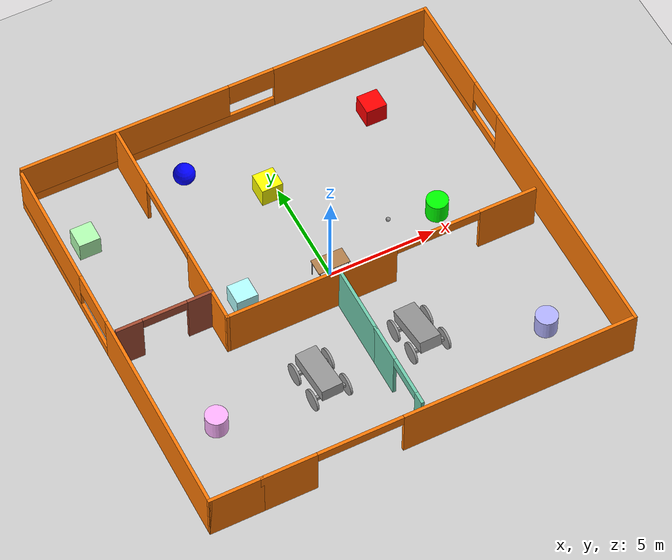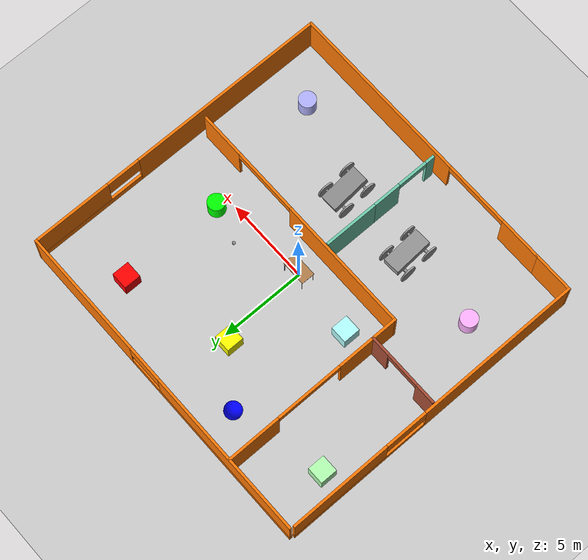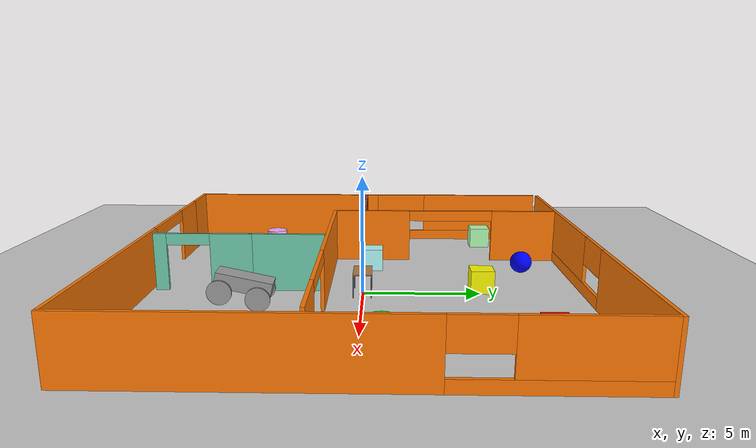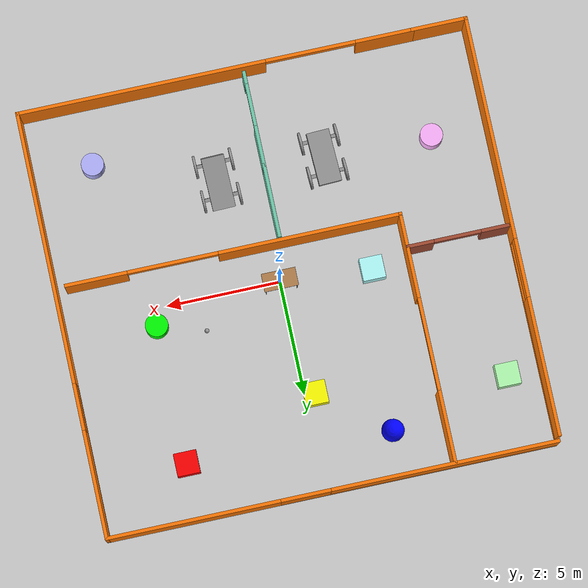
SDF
<sdf version="1.6">
 <world name="default">
  <model name="ground_plane">
   <static>1</static>
   <link name="link">
    <collision name="collision">
     <geometry><plane><normal>0 0 1</normal><size>100 100</size></plane></geometry>
     <surface>
      <contact><collide_bitmask>65535</collide_bitmask></contact>
      <friction><ode><mu>100</mu><mu2>50</mu2></ode></friction>
     </surface>
    </collision>
    <visual name="visual">
     <cast_shadows>0</cast_shadows>
     <geometry><plane><normal>0 0 1</normal><size>100 100</size></plane></geometry>
     <material>
      <script><uri>file://media/materials/scripts/gazebo.material</uri><name>Gazebo/Grey</name></script>
     </material>
    </visual>
   </link>
  </model>
  <plugin name="welcome_message" filename="libwelcome_message.so"/>
  <light name="sun" type="directional">
   <pose>0 0 10 0 -0 0</pose>
   <diffuse>0.8 0.8 0.8 1</diffuse>
   <specular>0.2 0.2 0.2 1</specular>
   <attenuation>
    <range>1000</range>
    <constant>0.9</constant>
    <linear>0.01</linear>
    <quadratic>0.001</quadratic>
   </attenuation>
   <direction>-0.5 0.1 -0.9</direction>
  </light>
  <model name="ground_plane">
   <static>1</static>
   <link name="link">
    <collision name="collision">
     <geometry><plane><normal>0 0 1</normal><size>100 100</size></plane></geometry>
     <surface>
      <contact><collide_bitmask>65535</collide_bitmask></contact>
      <friction><ode><mu>100</mu><mu2>50</mu2></ode></friction>
     </surface>
    </collision>
    <visual name="visual">
     <cast_shadows>0</cast_shadows>
     <geometry><plane><normal>0 0 1</normal><size>100 100</size></plane></geometry>
     <material>
      <script><uri>file://media/materials/scripts/gazebo.material</uri><name>Gazebo/Grey</name></script>
     </material>
    </visual>
   </link>
  </model>
  <gravity>0 0 -9.8</gravity>
  <magnetic_field>6e-06 2.3e-05 -4.2e-05</magnetic_field>
  <atmosphere type="adiabatic"/>
  <physics name="default_physics" default="0" type="ode">
   <max_step_size>0.001</max_step_size>
   <real_time_factor>1</real_time_factor>
   <real_time_update_rate>1000</real_time_update_rate>
  </physics>
  <scene><ambient>0.4 0.4 0.4 1</ambient><background>0.7 0.7 0.7 1</background><shadows>1</shadows></scene>
  <audio><device>default</device></audio>
  <spherical_coordinates>
   <surface_model>EARTH_WGS84</surface_model>
   <latitude_deg>0</latitude_deg>
   <longitude_deg>0</longitude_deg>
   <elevation>0</elevation>
   <heading_deg>0</heading_deg>
  </spherical_coordinates>
  <model name="table">
   <static>1</static>
   <link name="link">
    <collision name="surface">
     <pose>0 0 1 0 -0 0</pose>
     <geometry><box><size>1.5 0.8 0.03</size></box></geometry>
     <surface><friction><ode><mu>0.6</mu><mu2>0.6</mu2></ode></friction></surface>
    </collision>
    <visual name="visual1">
     <pose>0 0 1 0 -0 0</pose>
     <geometry><box><size>1.5 0.8 0.03</size></box></geometry>
     <material>
      <script><uri>file://media/materials/scripts/gazebo.material</uri><name>Gazebo/Wood</name></script>
     </material>
    </visual>
    <collision name="front_left_leg">
     <pose>0.68 0.38 0.5 0 -0 0</pose>
     <geometry><cylinder><radius>0.02</radius><length>1</length></cylinder></geometry>
    </collision>
    <visual name="front_left_leg">
     <pose>0.68 0.38 0.5 0 -0 0</pose>
     <geometry><cylinder><radius>0.02</radius><length>1</length></cylinder></geometry>
     <material>
      <script><uri>file://media/materials/scripts/gazebo.material</uri><name>Gazebo/Grey</name></script>
     </material>
    </visual>
    <collision name="front_right_leg">
     <pose>0.68 -0.38 0.5 0 -0 0</pose>
     <geometry><cylinder><radius>0.02</radius><length>1</length></cylinder></geometry>
    </collision>
    <visual name="front_right_leg">
     <pose>0.68 -0.38 0.5 0 -0 0</pose>
     <geometry><cylinder><radius>0.02</radius><length>1</length></cylinder></geometry>
     <material>
      <script><uri>file://media/materials/scripts/gazebo.material</uri><name>Gazebo/Grey</name></script>
     </material>
    </visual>
    <collision name="back_right_leg">
     <pose>-0.68 -0.38 0.5 0 -0 0</pose>
     <geometry><cylinder><radius>0.02</radius><length>1</length></cylinder></geometry>
    </collision>
    <visual name="back_right_leg">
     <pose>-0.68 -0.38 0.5 0 -0 0</pose>
     <geometry><cylinder><radius>0.02</radius><length>1</length></cylinder></geometry>
     <material>
      <script><uri>file://media/materials/scripts/gazebo.material</uri><name>Gazebo/Grey</name></script>
     </material>
    </visual>
    <collision name="back_left_leg">
     <pose>-0.68 0.38 0.5 0 -0 0</pose>
     <geometry><cylinder><radius>0.02</radius><length>1</length></cylinder></geometry>
    </collision>
    <visual name="back_left_leg">
     <pose>-0.68 0.38 0.5 0 -0 0</pose>
     <geometry><cylinder><radius>0.02</radius><length>1</length></cylinder></geometry>
     <material>
      <script><uri>file://media/materials/scripts/gazebo.material</uri><name>Gazebo/Grey</name></script>
     </material>
    </visual>
   </link>
  </model>
  <model name="buildingmodel">
   <pose>-0.320081 0.0932 0 0 -0 0</pose>
   <link name="Wall_16">
    <pose>1.175 -9.3 0 0 -0 0</pose>
    <visual name="Wall_16_Visual_0">
     <pose>-7.45803 0 1.25 0 -0 0</pose>
     <geometry><box><size>2.58395 0.15 2.5</size></box></geometry>
     <material>
      <script><uri>file://media/materials/scripts/gazebo.material</uri><name>Gazebo/Grey</name></script>
      <ambient>0.996078 0.47451 0.0196078 1</ambient>
     </material>
     <meta><layer>0</layer></meta>
    </visual>
    <collision name="Wall_16_Collision_0">
     <geometry><box><size>2.58395 0.15 2.5</size></box></geometry>
     <pose>-7.45803 0 1.25 0 -0 0</pose>
    </collision>
    <visual name="Wall_16_Visual_1">
     <pose>3.26705 0 1.25 0 -0 0</pose>
     <geometry><box><size>10.9659 0.15 2.5</size></box></geometry>
     <material>
      <script><uri>file://media/materials/scripts/gazebo.material</uri><name>Gazebo/Grey</name></script>
      <ambient>0.996078 0.47451 0.0196078 1</ambient>
     </material>
     <meta><layer>0</layer></meta>
    </visual>
    <collision name="Wall_16_Collision_1">
     <geometry><box><size>10.9659 0.15 2.5</size></box></geometry>
     <pose>3.26705 0 1.25 0 -0 0</pose>
    </collision>
    <visual name="Wall_16_Visual_2">
     <pose>-4.19098 0 2.25 0 -0 0</pose>
     <geometry><box><size>3.95016 0.15 0.5</size></box></geometry>
     <material>
      <script><uri>file://media/materials/scripts/gazebo.material</uri><name>Gazebo/Grey</name></script>
      <ambient>0.996078 0.47451 0.0196078 1</ambient>
     </material>
     <meta><layer>0</layer></meta>
    </visual>
    <collision name="Wall_16_Collision_2">
     <geometry><box><size>3.95016 0.15 0.5</size></box></geometry>
     <pose>-4.19098 0 2.25 0 -0 0</pose>
    </collision>
   </link>
   <link name="Wall_19">
    <collision name="Wall_19_Collision">
     <geometry><box><size>2.5 0.15 2.5</size></box></geometry>
     <pose>0 0 1.25 0 -0 0</pose>
    </collision>
    <visual name="Wall_19_Visual">
     <pose>0 0 1.25 0 -0 0</pose>
     <geometry><box><size>2.5 0.15 2.5</size></box></geometry>
     <material>
      <script><uri>file://media/materials/scripts/gazebo.material</uri><name>Gazebo/Grey</name></script>
      <ambient>0.996078 0.47451 0.0196078 1</ambient>
     </material>
     <meta><layer>0</layer></meta>
    </visual>
    <pose>-8.675 -9.3 0 0 -0 3.14159</pose>
   </link>
   <link name="Wall_39">
    <pose>9.85 0 0 0 -0 1.5708</pose>
    <visual name="Wall_39_Visual_0">
     <pose>-3.40224 0 1.25 0 -0 0</pose>
     <geometry><box><size>11.9455 0.15 2.5</size></box></geometry>
     <material>
      <script><uri>file://media/materials/scripts/gazebo.material</uri><name>Gazebo/Grey</name></script>
      <ambient>0.996078 0.47451 0.0196078 1</ambient>
     </material>
     <meta><layer>0</layer></meta>
    </visual>
    <collision name="Wall_39_Collision_0">
     <geometry><box><size>11.9455 0.15 2.5</size></box></geometry>
     <pose>-3.40224 0 1.25 0 -0 0</pose>
    </collision>
    <visual name="Wall_39_Visual_1">
     <pose>5.97276 0 0.25 0 -0 0</pose>
     <geometry><box><size>6.80448 0.15 0.5</size></box></geometry>
     <material>
      <script><uri>file://media/materials/scripts/gazebo.material</uri><name>Gazebo/Grey</name></script>
      <ambient>0.996078 0.47451 0.0196078 1</ambient>
     </material>
     <meta><layer>0</layer></meta>
    </visual>
    <collision name="Wall_39_Collision_1">
     <geometry><box><size>6.80448 0.15 0.5</size></box></geometry>
     <pose>5.97276 0 0.25 0 -0 0</pose>
    </collision>
    <visual name="Wall_39_Visual_2">
     <pose>6.99343 0 1.5 0 -0 0</pose>
     <geometry><box><size>4.76314 0.15 2</size></box></geometry>
     <material>
      <script><uri>file://media/materials/scripts/gazebo.material</uri><name>Gazebo/Grey</name></script>
      <ambient>0.996078 0.47451 0.0196078 1</ambient>
     </material>
     <meta><layer>0</layer></meta>
    </visual>
    <collision name="Wall_39_Collision_2">
     <geometry><box><size>4.76314 0.15 2</size></box></geometry>
     <pose>6.99343 0 1.5 0 -0 0</pose>
    </collision>
    <visual name="Wall_39_Visual_3">
     <pose>3.59119 0 1.9 0 -0 0</pose>
     <geometry><box><size>2.04134 0.15 1.2</size></box></geometry>
     <material>
      <script><uri>file://media/materials/scripts/gazebo.material</uri><name>Gazebo/Grey</name></script>
      <ambient>0.996078 0.47451 0.0196078 1</ambient>
     </material>
     <meta><layer>0</layer></meta>
    </visual>
    <collision name="Wall_39_Collision_3">
     <geometry><box><size>2.04134 0.15 1.2</size></box></geometry>
     <pose>3.59119 0 1.9 0 -0 0</pose>
    </collision>
   </link>
   <link name="Wall_40">
    <pose>0.05 9.3 0 0 -0 3.14159</pose>
    <visual name="Wall_40_Visual_0">
     <pose>-6.06574 0 1.25 0 -0 0</pose>
     <geometry><box><size>7.61852 0.15 2.5</size></box></geometry>
     <material>
      <script><uri>file://media/materials/scripts/gazebo.material</uri><name>Gazebo/Grey</name></script>
      <ambient>0.996078 0.47451 0.0196078 1</ambient>
     </material>
     <meta><layer>0</layer></meta>
    </visual>
    <collision name="Wall_40_Collision_0">
     <geometry><box><size>7.61852 0.15 2.5</size></box></geometry>
     <pose>-6.06574 0 1.25 0 -0 0</pose>
    </collision>
    <visual name="Wall_40_Visual_1">
     <pose>3.80926 0 0.25 0 -0 0</pose>
     <geometry><box><size>12.1315 0.15 0.5</size></box></geometry>
     <material>
      <script><uri>file://media/materials/scripts/gazebo.material</uri><name>Gazebo/Grey</name></script>
      <ambient>0.996078 0.47451 0.0196078 1</ambient>
     </material>
     <meta><layer>0</layer></meta>
    </visual>
    <collision name="Wall_40_Collision_1">
     <geometry><box><size>12.1315 0.15 0.5</size></box></geometry>
     <pose>3.80926 0 0.25 0 -0 0</pose>
    </collision>
    <visual name="Wall_40_Visual_2">
     <pose>4.90087 0 1.5 0 -0 0</pose>
     <geometry><box><size>9.94827 0.15 2</size></box></geometry>
     <material>
      <script><uri>file://media/materials/scripts/gazebo.material</uri><name>Gazebo/Grey</name></script>
      <ambient>0.996078 0.47451 0.0196078 1</ambient>
     </material>
     <meta><layer>0</layer></meta>
    </visual>
    <collision name="Wall_40_Collision_2">
     <geometry><box><size>9.94827 0.15 2</size></box></geometry>
     <pose>4.90087 0 1.5 0 -0 0</pose>
    </collision>
    <visual name="Wall_40_Visual_3">
     <pose>-1.16487 0 1.9 0 -0 0</pose>
     <geometry><box><size>2.18321 0.15 1.2</size></box></geometry>
     <material>
      <script><uri>file://media/materials/scripts/gazebo.material</uri><name>Gazebo/Grey</name></script>
      <ambient>0.996078 0.47451 0.0196078 1</ambient>
     </material>
     <meta><layer>0</layer></meta>
    </visual>
    <collision name="Wall_40_Collision_3">
     <geometry><box><size>2.18321 0.15 1.2</size></box></geometry>
     <pose>-1.16487 0 1.9 0 -0 0</pose>
    </collision>
   </link>
   <link name="Wall_42">
    <pose>-9.85 -0.125 0 0 -0 1.5708</pose>
    <visual name="Wall_42_Visual_0">
     <pose>-4.32759 0 1.25 0 -0 0</pose>
     <geometry><box><size>9.84482 0.15 2.5</size></box></geometry>
     <material>
      <script><uri>file://media/materials/scripts/gazebo.material</uri><name>Gazebo/Grey</name></script>
      <ambient>0.996078 0.47451 0.0196078 1</ambient>
     </material>
     <meta><layer>0</layer></meta>
    </visual>
    <collision name="Wall_42_Collision_0">
     <geometry><box><size>9.84482 0.15 2.5</size></box></geometry>
     <pose>-4.32759 0 1.25 0 -0 0</pose>
    </collision>
    <visual name="Wall_42_Visual_1">
     <pose>4.92241 0 0.25 0 -0 0</pose>
     <geometry><box><size>8.65518 0.15 0.5</size></box></geometry>
     <material>
      <script><uri>file://media/materials/scripts/gazebo.material</uri><name>Gazebo/Grey</name></script>
      <ambient>0.996078 0.47451 0.0196078 1</ambient>
     </material>
     <meta><layer>0</layer></meta>
    </visual>
    <collision name="Wall_42_Collision_1">
     <geometry><box><size>8.65518 0.15 0.5</size></box></geometry>
     <pose>4.92241 0 0.25 0 -0 0</pose>
    </collision>
    <visual name="Wall_42_Visual_2">
     <pose>6.20908 0 1.5 0 -0 0</pose>
     <geometry><box><size>6.08183 0.15 2</size></box></geometry>
     <material>
      <script><uri>file://media/materials/scripts/gazebo.material</uri><name>Gazebo/Grey</name></script>
      <ambient>0.996078 0.47451 0.0196078 1</ambient>
     </material>
     <meta><layer>0</layer></meta>
    </visual>
    <collision name="Wall_42_Collision_2">
     <geometry><box><size>6.08183 0.15 2</size></box></geometry>
     <pose>6.20908 0 1.5 0 -0 0</pose>
    </collision>
    <visual name="Wall_42_Visual_3">
     <pose>1.88149 0 1.9 0 -0 0</pose>
     <geometry><box><size>2.57335 0.15 1.2</size></box></geometry>
     <material>
      <script><uri>file://media/materials/scripts/gazebo.material</uri><name>Gazebo/Grey</name></script>
      <ambient>0.996078 0.47451 0.0196078 1</ambient>
     </material>
     <meta><layer>0</layer></meta>
    </visual>
    <collision name="Wall_42_Collision_3">
     <geometry><box><size>2.57335 0.15 1.2</size></box></geometry>
     <pose>1.88149 0 1.9 0 -0 0</pose>
    </collision>
   </link>
   <link name="Wall_45">
    <pose>2.02344 -1.60383 0 0 -0 3.14159</pose>
    <visual name="Wall_45_Visual_0">
     <pose>-6.0053 0 1.25 0 -0 0</pose>
     <geometry><box><size>2.7394 0.15 2.5</size></box></geometry>
     <material>
      <script><uri>file://media/materials/scripts/gazebo.material</uri><name>Gazebo/Grey</name></script>
      <ambient>0.996078 0.47451 0.0196078 1</ambient>
     </material>
     <meta><layer>0</layer></meta>
    </visual>
    <collision name="Wall_45_Collision_0">
     <geometry><box><size>2.7394 0.15 2.5</size></box></geometry>
     <pose>-6.0053 0 1.25 0 -0 0</pose>
    </collision>
    <visual name="Wall_45_Visual_1">
     <pose>3.35584 0 1.25 0 -0 0</pose>
     <geometry><box><size>8.03832 0.15 2.5</size></box></geometry>
     <material>
      <script><uri>file://media/materials/scripts/gazebo.material</uri><name>Gazebo/Grey</name></script>
      <ambient>0.996078 0.47451 0.0196078 1</ambient>
     </material>
     <meta><layer>0</layer></meta>
    </visual>
    <collision name="Wall_45_Collision_1">
     <geometry><box><size>8.03832 0.15 2.5</size></box></geometry>
     <pose>3.35584 0 1.25 0 -0 0</pose>
    </collision>
    <visual name="Wall_45_Visual_2">
     <pose>-2.64946 0 2.25 0 -0 0</pose>
     <geometry><box><size>3.97228 0.15 0.5</size></box></geometry>
     <material>
      <script><uri>file://media/materials/scripts/gazebo.material</uri><name>Gazebo/Grey</name></script>
      <ambient>0.996078 0.47451 0.0196078 1</ambient>
     </material>
     <meta><layer>0</layer></meta>
    </visual>
    <collision name="Wall_45_Collision_2">
     <geometry><box><size>3.97228 0.15 0.5</size></box></geometry>
     <pose>-2.64946 0 2.25 0 -0 0</pose>
    </collision>
   </link>
   <link name="Wall_46">
    <pose>-5.27656 3.82117 0 0 -0 1.5708</pose>
    <visual name="Wall_46_Visual_0">
     <pose>-3.61661 0 1.25 0 -0 0</pose>
     <geometry><box><size>3.76677 0.15 2.5</size></box></geometry>
     <material>
      <script><uri>file://media/materials/scripts/gazebo.material</uri><name>Gazebo/Grey</name></script>
      <ambient>0.996078 0.47451 0.0196078 1</ambient>
     </material>
     <meta><layer>0</layer></meta>
    </visual>
    <collision name="Wall_46_Collision_0">
     <geometry><box><size>3.76677 0.15 2.5</size></box></geometry>
     <pose>-3.61661 0 1.25 0 -0 0</pose>
    </collision>
    <visual name="Wall_46_Visual_1">
     <pose>3.9047 0 1.25 0 -0 0</pose>
     <geometry><box><size>3.19059 0.15 2.5</size></box></geometry>
     <material>
      <script><uri>file://media/materials/scripts/gazebo.material</uri><name>Gazebo/Grey</name></script>
      <ambient>0.996078 0.47451 0.0196078 1</ambient>
     </material>
     <meta><layer>0</layer></meta>
    </visual>
    <collision name="Wall_46_Collision_1">
     <geometry><box><size>3.19059 0.15 2.5</size></box></geometry>
     <pose>3.9047 0 1.25 0 -0 0</pose>
    </collision>
    <visual name="Wall_46_Visual_2">
     <pose>0.288089 0 2.25 0 -0 0</pose>
     <geometry><box><size>4.04264 0.15 0.5</size></box></geometry>
     <material>
      <script><uri>file://media/materials/scripts/gazebo.material</uri><name>Gazebo/Grey</name></script>
      <ambient>0.996078 0.47451 0.0196078 1</ambient>
     </material>
     <meta><layer>0</layer></meta>
    </visual>
    <collision name="Wall_46_Collision_2">
     <geometry><box><size>4.04264 0.15 0.5</size></box></geometry>
     <pose>0.288089 0 2.25 0 -0 0</pose>
    </collision>
   </link>
   <static>1</static>
  </model>
  <model name="model">
   <link name="link_0_clone">
    <inertial>
     <mass>1</mass>
     <inertia><ixx>0.145833</ixx><ixy>0</ixy><ixz>0</ixz><iyy>0.145833</iyy><iyz>0</iyz><izz>0.125</izz></inertia>
    </inertial>
    <pose>0.800049 0.773824 -0.030357 0 -0 0</pose>
    <visual name="visual">
     <pose>0 0 0 0 1.5707 0</pose>
     <geometry><cylinder><radius>0.5</radius><length>0.1</length></cylinder></geometry>
     <material>
      <lighting>1</lighting>
      <script><uri>file://media/materials/scripts/gazebo.material</uri><name>Gazebo/Grey</name></script>
      <shader type="vertex"><normal_map>__default__</normal_map></shader>
      <ambient>0.3 0.3 0.3 1</ambient>
      <diffuse>0.7 0.7 0.7 1</diffuse>
      <specular>0.01 0.01 0.01 1</specular>
      <emissive>0 0 0 1</emissive>
     </material>
    </visual>
    <collision name="collision">
     <pose>0 0 0 0 1.5707 0</pose>
     <geometry><cylinder><radius>0.5</radius><length>0.1</length></cylinder></geometry>
     <surface>
      <friction>
       <ode><mu>1</mu><mu2>1</mu2><fdir1>0 0 0</fdir1><slip1>0</slip1><slip2>0</slip2></ode>
       <torsional>
        <coefficient>1</coefficient>
        <patch_radius>0</patch_radius>
        <surface_radius>0</surface_radius>
        <use_patch_radius>1</use_patch_radius>
        <ode><slip>0</slip></ode>
       </torsional>
      </friction>
      <bounce><restitution_coefficient>0</restitution_coefficient><threshold>1e+06</threshold></bounce>
      <contact>
       <collide_without_contact>0</collide_without_contact>
       <collide_without_contact_bitmask>1</collide_without_contact_bitmask>
       <collide_bitmask>1</collide_bitmask>
       <ode>
        <soft_cfm>0</soft_cfm>
        <soft_erp>0.2</soft_erp>
        <kp>1e+13</kp>
        <kd>1</kd>
        <max_vel>0.01</max_vel>
        <min_depth>0</min_depth>
       </ode>
       <bullet>
        <split_impulse>1</split_impulse>
        <split_impulse_penetration_threshold>-0.01</split_impulse_penetration_threshold>
        <soft_cfm>0</soft_cfm>
        <soft_erp>0.2</soft_erp>
        <kp>1e+13</kp>
        <kd>1</kd>
       </bullet>
      </contact>
     </surface>
    </collision>
   </link>
   <link name="link_0_clone_clone">
    <inertial>
     <mass>1</mass>
     <inertia><ixx>0.145833</ixx><ixy>0</ixy><ixz>0</ixz><iyy>0.145833</iyy><iyz>0</iyz><izz>0.125</izz></inertia>
    </inertial>
    <pose>-0.800048 0.773824 -0.030357 0 -0 0</pose>
    <visual name="visual">
     <pose>0 0 0 0 1.5707 0</pose>
     <geometry><cylinder><radius>0.5</radius><length>0.1</length></cylinder></geometry>
     <material>
      <lighting>1</lighting>
      <script><uri>file://media/materials/scripts/gazebo.material</uri><name>Gazebo/Grey</name></script>
      <shader type="vertex"><normal_map>__default__</normal_map></shader>
      <ambient>0.3 0.3 0.3 1</ambient>
      <diffuse>0.7 0.7 0.7 1</diffuse>
      <specular>0.01 0.01 0.01 1</specular>
      <emissive>0 0 0 1</emissive>
     </material>
    </visual>
    <collision name="collision">
     <pose>0 0 0 0 1.5707 0</pose>
     <geometry><cylinder><radius>0.5</radius><length>0.1</length></cylinder></geometry>
     <surface>
      <friction>
       <ode><mu>1</mu><mu2>1</mu2><fdir1>0 0 0</fdir1><slip1>0</slip1><slip2>0</slip2></ode>
       <torsional>
        <coefficient>1</coefficient>
        <patch_radius>0</patch_radius>
        <surface_radius>0</surface_radius>
        <use_patch_radius>1</use_patch_radius>
        <ode><slip>0</slip></ode>
       </torsional>
      </friction>
      <bounce><restitution_coefficient>0</restitution_coefficient><threshold>1e+06</threshold></bounce>
      <contact>
       <collide_without_contact>0</collide_without_contact>
       <collide_without_contact_bitmask>1</collide_without_contact_bitmask>
       <collide_bitmask>1</collide_bitmask>
       <ode>
        <soft_cfm>0</soft_cfm>
        <soft_erp>0.2</soft_erp>
        <kp>1e+13</kp>
        <kd>1</kd>
        <max_vel>0.01</max_vel>
        <min_depth>0</min_depth>
       </ode>
       <bullet>
        <split_impulse>1</split_impulse>
        <split_impulse_penetration_threshold>-0.01</split_impulse_penetration_threshold>
        <soft_cfm>0</soft_cfm>
        <soft_erp>0.2</soft_erp>
        <kp>1e+13</kp>
        <kd>1</kd>
       </bullet>
      </contact>
     </surface>
    </collision>
   </link>
   <link name="link_0_clone_clone_clone">
    <inertial>
     <mass>1</mass>
     <inertia><ixx>0.145833</ixx><ixy>0</ixy><ixz>0</ixz><iyy>0.145833</iyy><iyz>0</iyz><izz>0.125</izz></inertia>
    </inertial>
    <pose>-0.800048 -0.758676 -0.062857 0 -0 0</pose>
    <visual name="visual">
     <pose>0 0 0 0 1.5707 0</pose>
     <geometry><cylinder><radius>0.5</radius><length>0.1</length></cylinder></geometry>
     <material>
      <lighting>1</lighting>
      <script><uri>file://media/materials/scripts/gazebo.material</uri><name>Gazebo/Grey</name></script>
      <shader type="vertex"><normal_map>__default__</normal_map></shader>
      <ambient>0.3 0.3 0.3 1</ambient>
      <diffuse>0.7 0.7 0.7 1</diffuse>
      <specular>0.01 0.01 0.01 1</specular>
      <emissive>0 0 0 1</emissive>
     </material>
    </visual>
    <collision name="collision">
     <pose>0 0 0 0 1.5707 0</pose>
     <geometry><cylinder><radius>0.5</radius><length>0.1</length></cylinder></geometry>
     <surface>
      <friction>
       <ode><mu>1</mu><mu2>1</mu2><fdir1>0 0 0</fdir1><slip1>0</slip1><slip2>0</slip2></ode>
       <torsional>
        <coefficient>1</coefficient>
        <patch_radius>0</patch_radius>
        <surface_radius>0</surface_radius>
        <use_patch_radius>1</use_patch_radius>
        <ode><slip>0</slip></ode>
       </torsional>
      </friction>
      <bounce><restitution_coefficient>0</restitution_coefficient><threshold>1e+06</threshold></bounce>
      <contact>
       <collide_without_contact>0</collide_without_contact>
       <collide_without_contact_bitmask>1</collide_without_contact_bitmask>
       <collide_bitmask>1</collide_bitmask>
       <ode>
        <soft_cfm>0</soft_cfm>
        <soft_erp>0.2</soft_erp>
        <kp>1e+13</kp>
        <kd>1</kd>
        <max_vel>0.01</max_vel>
        <min_depth>0</min_depth>
       </ode>
       <bullet>
        <split_impulse>1</split_impulse>
        <split_impulse_penetration_threshold>-0.01</split_impulse_penetration_threshold>
        <soft_cfm>0</soft_cfm>
        <soft_erp>0.2</soft_erp>
        <kp>1e+13</kp>
        <kd>1</kd>
       </bullet>
      </contact>
     </surface>
    </collision>
   </link>
   <link name="link_0_clone_clone_clone_0">
    <inertial>
     <mass>1</mass>
     <inertia><ixx>0.145833</ixx><ixy>0</ixy><ixz>0</ixz><iyy>0.145833</iyy><iyz>0</iyz><izz>0.125</izz></inertia>
    </inertial>
    <pose>0.800049 -0.758676 -0.062857 0 -0 0</pose>
    <visual name="visual">
     <pose>0 0 0 0 1.5707 0</pose>
     <geometry><cylinder><radius>0.5</radius><length>0.1</length></cylinder></geometry>
     <material>
      <lighting>1</lighting>
      <script><uri>file://media/materials/scripts/gazebo.material</uri><name>Gazebo/Grey</name></script>
      <shader type="vertex"><normal_map>__default__</normal_map></shader>
      <ambient>0.3 0.3 0.3 1</ambient>
      <diffuse>0.7 0.7 0.7 1</diffuse>
      <specular>0.01 0.01 0.01 1</specular>
      <emissive>0 0 0 1</emissive>
     </material>
    </visual>
    <collision name="collision">
     <pose>0 0 0 0 1.5707 0</pose>
     <geometry><cylinder><radius>0.5</radius><length>0.1</length></cylinder></geometry>
     <surface>
      <friction>
       <ode><mu>1</mu><mu2>1</mu2><fdir1>0 0 0</fdir1><slip1>0</slip1><slip2>0</slip2></ode>
       <torsional>
        <coefficient>1</coefficient>
        <patch_radius>0</patch_radius>
        <surface_radius>0</surface_radius>
        <use_patch_radius>1</use_patch_radius>
        <ode><slip>0</slip></ode>
       </torsional>
      </friction>
      <bounce><restitution_coefficient>0</restitution_coefficient><threshold>1e+06</threshold></bounce>
      <contact>
       <collide_without_contact>0</collide_without_contact>
       <collide_without_contact_bitmask>1</collide_without_contact_bitmask>
       <collide_bitmask>1</collide_bitmask>
       <ode>
        <soft_cfm>0</soft_cfm>
        <soft_erp>0.2</soft_erp>
        <kp>1e+13</kp>
        <kd>1</kd>
        <max_vel>0.01</max_vel>
        <min_depth>0</min_depth>
       </ode>
       <bullet>
        <split_impulse>1</split_impulse>
        <split_impulse_penetration_threshold>-0.01</split_impulse_penetration_threshold>
        <soft_cfm>0</soft_cfm>
        <soft_erp>0.2</soft_erp>
        <kp>1e+13</kp>
        <kd>1</kd>
       </bullet>
      </contact>
     </surface>
    </collision>
   </link>
   <link name="link_1">
    <inertial>
     <mass>1</mass>
     <inertia>
      <ixx>0.166667</ixx>
      <ixy>0</ixy>
      <ixz>0</ixz>
      <iyy>0.166667</iyy>
      <iyz>0</iyz>
      <izz>0.166667</izz>
     </inertia>
    </inertial>
    <pose>0 0.741324 -0.062857 0 -0 0</pose>
    <visual name="visual">
     <geometry><box><size>1.5 0.15 0.15</size></box></geometry>
     <material>
      <lighting>1</lighting>
      <script><uri>file://media/materials/scripts/gazebo.material</uri><name>Gazebo/Grey</name></script>
      <shader type="vertex"><normal_map>__default__</normal_map></shader>
      <ambient>0.3 0.3 0.3 1</ambient>
      <diffuse>0.7 0.7 0.7 1</diffuse>
      <specular>0.01 0.01 0.01 1</specular>
      <emissive>0 0 0 1</emissive>
     </material>
    </visual>
    <collision name="collision">
     <geometry><box><size>1.5 0.15 0.15</size></box></geometry>
     <surface>
      <friction>
       <ode><mu>1</mu><mu2>1</mu2><fdir1>0 0 0</fdir1><slip1>0</slip1><slip2>0</slip2></ode>
       <torsional>
        <coefficient>1</coefficient>
        <patch_radius>0</patch_radius>
        <surface_radius>0</surface_radius>
        <use_patch_radius>1</use_patch_radius>
        <ode><slip>0</slip></ode>
       </torsional>
      </friction>
      <bounce><restitution_coefficient>0</restitution_coefficient><threshold>1e+06</threshold></bounce>
      <contact>
       <collide_without_contact>0</collide_without_contact>
       <collide_without_contact_bitmask>1</collide_without_contact_bitmask>
       <collide_bitmask>1</collide_bitmask>
       <ode>
        <soft_cfm>0</soft_cfm>
        <soft_erp>0.2</soft_erp>
        <kp>1e+13</kp>
        <kd>1</kd>
        <max_vel>0.01</max_vel>
        <min_depth>0</min_depth>
       </ode>
       <bullet>
        <split_impulse>1</split_impulse>
        <split_impulse_penetration_threshold>-0.01</split_impulse_penetration_threshold>
        <soft_cfm>0</soft_cfm>
        <soft_erp>0.2</soft_erp>
        <kp>1e+13</kp>
        <kd>1</kd>
       </bullet>
      </contact>
     </surface>
    </collision>
   </link>
   <link name="link_1_clone">
    <inertial>
     <mass>1</mass>
     <inertia>
      <ixx>0.166667</ixx>
      <ixy>0</ixy>
      <ixz>0</ixz>
      <iyy>0.166667</iyy>
      <iyz>0</iyz>
      <izz>0.166667</izz>
     </inertia>
    </inertial>
    <pose>0 -0.758676 -0.062857 0 -0 0</pose>
    <visual name="visual">
     <geometry><box><size>1.5 0.15 0.15</size></box></geometry>
     <material>
      <lighting>1</lighting>
      <script><uri>file://media/materials/scripts/gazebo.material</uri><name>Gazebo/Grey</name></script>
      <shader type="vertex"><normal_map>__default__</normal_map></shader>
      <ambient>0.3 0.3 0.3 1</ambient>
      <diffuse>0.7 0.7 0.7 1</diffuse>
      <specular>0.01 0.01 0.01 1</specular>
      <emissive>0 0 0 1</emissive>
     </material>
    </visual>
    <collision name="collision">
     <geometry><box><size>1.5 0.15 0.15</size></box></geometry>
     <surface>
      <friction>
       <ode><mu>1</mu><mu2>1</mu2><fdir1>0 0 0</fdir1><slip1>0</slip1><slip2>0</slip2></ode>
       <torsional>
        <coefficient>1</coefficient>
        <patch_radius>0</patch_radius>
        <surface_radius>0</surface_radius>
        <use_patch_radius>1</use_patch_radius>
        <ode><slip>0</slip></ode>
       </torsional>
      </friction>
      <bounce><restitution_coefficient>0</restitution_coefficient><threshold>1e+06</threshold></bounce>
      <contact>
       <collide_without_contact>0</collide_without_contact>
       <collide_without_contact_bitmask>1</collide_without_contact_bitmask>
       <collide_bitmask>1</collide_bitmask>
       <ode>
        <soft_cfm>0</soft_cfm>
        <soft_erp>0.2</soft_erp>
        <kp>1e+13</kp>
        <kd>1</kd>
        <max_vel>0.01</max_vel>
        <min_depth>0</min_depth>
       </ode>
       <bullet>
        <split_impulse>1</split_impulse>
        <split_impulse_penetration_threshold>-0.01</split_impulse_penetration_threshold>
        <soft_cfm>0</soft_cfm>
        <soft_erp>0.2</soft_erp>
        <kp>1e+13</kp>
        <kd>1</kd>
       </bullet>
      </contact>
     </surface>
    </collision>
   </link>
   <link name="link_4">
    <inertial>
     <mass>2.30548</mass>
     <inertia><ixx>1.2133</ixx><ixy>0</ixy><ixz>0</ixz><iyy>0.384247</iyy><iyz>0</iyz><izz>1.2133</izz></inertia>
    </inertial>
    <pose>0 0.069782 0.312143 0 -0 0</pose>
    <visual name="visual">
     <geometry><box><size>1 2.30548 0.6</size></box></geometry>
     <material>
      <lighting>1</lighting>
      <script><uri>file://media/materials/scripts/gazebo.material</uri><name>Gazebo/Grey</name></script>
      <emissive>0 0 0 1</emissive>
      <shader type="vertex"><normal_map>__default__</normal_map></shader>
      <ambient>0.3 0.3 0.3 1</ambient>
      <diffuse>0.7 0.7 0.7 1</diffuse>
      <specular>0.01 0.01 0.01 1</specular>
     </material>
    </visual>
    <collision name="collision">
     <geometry><box><size>1 2.30548 0.6</size></box></geometry>
     <surface>
      <friction>
       <ode><mu>1</mu><mu2>1</mu2><fdir1>0 0 0</fdir1><slip1>0</slip1><slip2>0</slip2></ode>
       <torsional>
        <coefficient>1</coefficient>
        <patch_radius>0</patch_radius>
        <surface_radius>0</surface_radius>
        <use_patch_radius>1</use_patch_radius>
        <ode><slip>0</slip></ode>
       </torsional>
      </friction>
      <bounce><restitution_coefficient>0</restitution_coefficient><threshold>1e+06</threshold></bounce>
      <contact>
       <collide_without_contact>0</collide_without_contact>
       <collide_without_contact_bitmask>1</collide_without_contact_bitmask>
       <collide_bitmask>1</collide_bitmask>
       <ode>
        <soft_cfm>0</soft_cfm>
        <soft_erp>0.2</soft_erp>
        <kp>1e+13</kp>
        <kd>1</kd>
        <max_vel>0.01</max_vel>
        <min_depth>0</min_depth>
       </ode>
       <bullet>
        <split_impulse>1</split_impulse>
        <split_impulse_penetration_threshold>-0.01</split_impulse_penetration_threshold>
        <soft_cfm>0</soft_cfm>
        <soft_erp>0.2</soft_erp>
        <kp>1e+13</kp>
        <kd>1</kd>
       </bullet>
      </contact>
     </surface>
    </collision>
   </link>
   <joint name="link_1_JOINT_2" type="revolute">
    <parent>link_1</parent>
    <child>link_0_clone</child>
    <axis>
     <xyz>1 0 0</xyz>
     <use_parent_model_frame>0</use_parent_model_frame>
     <limit>
      <lower>-1.79769e+308</lower>
      <upper>1.79769e+308</upper>
      <effort>-1</effort>
      <velocity>-1</velocity>
     </limit>
     <dynamics>
      <spring_reference>0</spring_reference>
      <spring_stiffness>0</spring_stiffness>
      <damping>0</damping>
     </dynamics>
    </axis>
    <physics>
     <ode><limit><cfm>0</cfm><erp>0.2</erp></limit><suspension><cfm>0</cfm><erp>0.2</erp></suspension></ode>
    </physics>
   </joint>
   <joint name="link_1_JOINT_3" type="revolute">
    <parent>link_1</parent>
    <child>link_0_clone_clone</child>
    <axis>
     <xyz>1 0 0</xyz>
     <use_parent_model_frame>0</use_parent_model_frame>
     <limit>
      <lower>-1.79769e+308</lower>
      <upper>1.79769e+308</upper>
      <effort>-1</effort>
      <velocity>-1</velocity>
     </limit>
     <dynamics>
      <spring_reference>0</spring_reference>
      <spring_stiffness>0</spring_stiffness>
      <damping>0</damping>
     </dynamics>
    </axis>
    <physics>
     <ode><limit><cfm>0</cfm><erp>0.2</erp></limit><suspension><cfm>0</cfm><erp>0.2</erp></suspension></ode>
    </physics>
   </joint>
   <joint name="link_1_JOINT_4" type="revolute">
    <parent>link_1</parent>
    <child>link_1_clone</child>
    <axis>
     <xyz>1 0 0</xyz>
     <use_parent_model_frame>0</use_parent_model_frame>
     <limit>
      <lower>-1.79769e+308</lower>
      <upper>1.79769e+308</upper>
      <effort>-1</effort>
      <velocity>-1</velocity>
     </limit>
     <dynamics>
      <spring_reference>0</spring_reference>
      <spring_stiffness>0</spring_stiffness>
      <damping>0</damping>
     </dynamics>
    </axis>
    <physics>
     <ode><limit><cfm>0</cfm><erp>0.2</erp></limit><suspension><cfm>0</cfm><erp>0.2</erp></suspension></ode>
    </physics>
   </joint>
   <joint name="link_1_JOINT_7" type="revolute">
    <parent>link_1</parent>
    <child>link_4</child>
    <axis>
     <xyz>1 0 0</xyz>
     <use_parent_model_frame>0</use_parent_model_frame>
     <limit>
      <lower>-1.79769e+308</lower>
      <upper>1.79769e+308</upper>
      <effort>-1</effort>
      <velocity>-1</velocity>
     </limit>
     <dynamics>
      <spring_reference>0</spring_reference>
      <spring_stiffness>0</spring_stiffness>
      <damping>0</damping>
     </dynamics>
    </axis>
    <physics>
     <ode><limit><cfm>0</cfm><erp>0.2</erp></limit><suspension><cfm>0</cfm><erp>0.2</erp></suspension></ode>
    </physics>
   </joint>
   <joint name="link_1_JOINT_8" type="revolute">
    <parent>link_1</parent>
    <child>link_4</child>
    <axis>
     <xyz>1 0 0</xyz>
     <use_parent_model_frame>0</use_parent_model_frame>
     <limit>
      <lower>-1.79769e+308</lower>
      <upper>1.79769e+308</upper>
      <effort>-1</effort>
      <velocity>-1</velocity>
     </limit>
     <dynamics>
      <spring_reference>0</spring_reference>
      <spring_stiffness>0</spring_stiffness>
      <damping>0</damping>
     </dynamics>
    </axis>
    <physics>
     <ode><limit><cfm>0</cfm><erp>0.2</erp></limit><suspension><cfm>0</cfm><erp>0.2</erp></suspension></ode>
    </physics>
   </joint>
   <joint name="link_1_clone_JOINT_5" type="revolute">
    <parent>link_1_clone</parent>
    <child>link_0_clone_clone_clone</child>
    <axis>
     <xyz>1 0 0</xyz>
     <use_parent_model_frame>0</use_parent_model_frame>
     <limit>
      <lower>-1.79769e+308</lower>
      <upper>1.79769e+308</upper>
      <effort>-1</effort>
      <velocity>-1</velocity>
     </limit>
     <dynamics>
      <spring_reference>0</spring_reference>
      <spring_stiffness>0</spring_stiffness>
      <damping>0</damping>
     </dynamics>
    </axis>
    <physics>
     <ode><limit><cfm>0</cfm><erp>0.2</erp></limit><suspension><cfm>0</cfm><erp>0.2</erp></suspension></ode>
    </physics>
   </joint>
   <joint name="link_1_clone_JOINT_6" type="revolute">
    <parent>link_1_clone</parent>
    <child>link_0_clone_clone_clone_0</child>
    <axis>
     <xyz>1 0 0</xyz>
     <use_parent_model_frame>0</use_parent_model_frame>
     <limit>
      <lower>-1.79769e+308</lower>
      <upper>1.79769e+308</upper>
      <effort>-1</effort>
      <velocity>-1</velocity>
     </limit>
     <dynamics>
      <spring_reference>0</spring_reference>
      <spring_stiffness>0</spring_stiffness>
      <damping>0</damping>
     </dynamics>
    </axis>
    <physics>
     <ode><limit><cfm>0</cfm><erp>0.2</erp></limit><suspension><cfm>0</cfm><erp>0.2</erp></suspension></ode>
    </physics>
   </joint>
   <joint name="link_1_clone_JOINT_9" type="revolute">
    <parent>link_1_clone</parent>
    <child>link_4</child>
    <axis>
     <xyz>1 0 0</xyz>
     <use_parent_model_frame>0</use_parent_model_frame>
     <limit>
      <lower>-1.79769e+308</lower>
      <upper>1.79769e+308</upper>
      <effort>-1</effort>
      <velocity>-1</velocity>
     </limit>
     <dynamics>
      <spring_reference>0</spring_reference>
      <spring_stiffness>0</spring_stiffness>
      <damping>0</damping>
     </dynamics>
    </axis>
    <physics>
     <ode><limit><cfm>0</cfm><erp>0.2</erp></limit><suspension><cfm>0</cfm><erp>0.2</erp></suspension></ode>
    </physics>
   </joint>
   <static>0</static>
   <pose>-2.98182 -4.9047 0.593807 -0.082213 1e-06 0.040703</pose>
  </model>
  <model name="model_clone">
   <link name="link_0_clone">
    <inertial>
     <mass>1</mass>
     <inertia><ixx>0.145833</ixx><ixy>0</ixy><ixz>0</ixz><iyy>0.145833</iyy><iyz>0</iyz><izz>0.125</izz></inertia>
    </inertial>
    <pose>0.800049 0.773824 -0.030357 0 -0 0</pose>
    <visual name="visual">
     <pose>0 0 0 0 1.5707 0</pose>
     <geometry><cylinder><radius>0.5</radius><length>0.1</length></cylinder></geometry>
     <material>
      <lighting>1</lighting>
      <script><uri>file://media/materials/scripts/gazebo.material</uri><name>Gazebo/Grey</name></script>
      <shader type="vertex"><normal_map>__default__</normal_map></shader>
      <ambient>0.3 0.3 0.3 1</ambient>
      <diffuse>0.7 0.7 0.7 1</diffuse>
      <specular>0.01 0.01 0.01 1</specular>
      <emissive>0 0 0 1</emissive>
     </material>
    </visual>
    <collision name="collision">
     <pose>0 0 0 0 1.5707 0</pose>
     <geometry><cylinder><radius>0.5</radius><length>0.1</length></cylinder></geometry>
     <surface>
      <friction>
       <ode><mu>1</mu><mu2>1</mu2><fdir1>0 0 0</fdir1><slip1>0</slip1><slip2>0</slip2></ode>
       <torsional>
        <coefficient>1</coefficient>
        <patch_radius>0</patch_radius>
        <surface_radius>0</surface_radius>
        <use_patch_radius>1</use_patch_radius>
        <ode><slip>0</slip></ode>
       </torsional>
      </friction>
      <bounce><restitution_coefficient>0</restitution_coefficient><threshold>1e+06</threshold></bounce>
      <contact>
       <collide_without_contact>0</collide_without_contact>
       <collide_without_contact_bitmask>1</collide_without_contact_bitmask>
       <collide_bitmask>1</collide_bitmask>
       <ode>
        <soft_cfm>0</soft_cfm>
        <soft_erp>0.2</soft_erp>
        <kp>1e+13</kp>
        <kd>1</kd>
        <max_vel>0.01</max_vel>
        <min_depth>0</min_depth>
       </ode>
       <bullet>
        <split_impulse>1</split_impulse>
        <split_impulse_penetration_threshold>-0.01</split_impulse_penetration_threshold>
        <soft_cfm>0</soft_cfm>
        <soft_erp>0.2</soft_erp>
        <kp>1e+13</kp>
        <kd>1</kd>
       </bullet>
      </contact>
     </surface>
    </collision>
   </link>
   <link name="link_0_clone_clone">
    <inertial>
     <mass>1</mass>
     <inertia><ixx>0.145833</ixx><ixy>0</ixy><ixz>0</ixz><iyy>0.145833</iyy><iyz>0</iyz><izz>0.125</izz></inertia>
    </inertial>
    <pose>-0.800048 0.773824 -0.030357 0 -0 0</pose>
    <visual name="visual">
     <pose>0 0 0 0 1.5707 0</pose>
     <geometry><cylinder><radius>0.5</radius><length>0.1</length></cylinder></geometry>
     <material>
      <lighting>1</lighting>
      <script><uri>file://media/materials/scripts/gazebo.material</uri><name>Gazebo/Grey</name></script>
      <shader type="vertex"><normal_map>__default__</normal_map></shader>
      <ambient>0.3 0.3 0.3 1</ambient>
      <diffuse>0.7 0.7 0.7 1</diffuse>
      <specular>0.01 0.01 0.01 1</specular>
      <emissive>0 0 0 1</emissive>
     </material>
    </visual>
    <collision name="collision">
     <pose>0 0 0 0 1.5707 0</pose>
     <geometry><cylinder><radius>0.5</radius><length>0.1</length></cylinder></geometry>
     <surface>
      <friction>
       <ode><mu>1</mu><mu2>1</mu2><fdir1>0 0 0</fdir1><slip1>0</slip1><slip2>0</slip2></ode>
       <torsional>
        <coefficient>1</coefficient>
        <patch_radius>0</patch_radius>
        <surface_radius>0</surface_radius>
        <use_patch_radius>1</use_patch_radius>
        <ode><slip>0</slip></ode>
       </torsional>
      </friction>
      <bounce><restitution_coefficient>0</restitution_coefficient><threshold>1e+06</threshold></bounce>
      <contact>
       <collide_without_contact>0</collide_without_contact>
       <collide_without_contact_bitmask>1</collide_without_contact_bitmask>
       <collide_bitmask>1</collide_bitmask>
       <ode>
        <soft_cfm>0</soft_cfm>
        <soft_erp>0.2</soft_erp>
        <kp>1e+13</kp>
        <kd>1</kd>
        <max_vel>0.01</max_vel>
        <min_depth>0</min_depth>
       </ode>
       <bullet>
        <split_impulse>1</split_impulse>
        <split_impulse_penetration_threshold>-0.01</split_impulse_penetration_threshold>
        <soft_cfm>0</soft_cfm>
        <soft_erp>0.2</soft_erp>
        <kp>1e+13</kp>
        <kd>1</kd>
       </bullet>
      </contact>
     </surface>
    </collision>
   </link>
   <link name="link_0_clone_clone_clone">
    <inertial>
     <mass>1</mass>
     <inertia><ixx>0.145833</ixx><ixy>0</ixy><ixz>0</ixz><iyy>0.145833</iyy><iyz>0</iyz><izz>0.125</izz></inertia>
    </inertial>
    <pose>-0.800048 -0.758676 -0.062857 0 -0 0</pose>
    <visual name="visual">
     <pose>0 0 0 0 1.5707 0</pose>
     <geometry><cylinder><radius>0.5</radius><length>0.1</length></cylinder></geometry>
     <material>
      <lighting>1</lighting>
      <script><uri>file://media/materials/scripts/gazebo.material</uri><name>Gazebo/Grey</name></script>
      <shader type="vertex"><normal_map>__default__</normal_map></shader>
      <ambient>0.3 0.3 0.3 1</ambient>
      <diffuse>0.7 0.7 0.7 1</diffuse>
      <specular>0.01 0.01 0.01 1</specular>
      <emissive>0 0 0 1</emissive>
     </material>
    </visual>
    <collision name="collision">
     <pose>0 0 0 0 1.5707 0</pose>
     <geometry><cylinder><radius>0.5</radius><length>0.1</length></cylinder></geometry>
     <surface>
      <friction>
       <ode><mu>1</mu><mu2>1</mu2><fdir1>0 0 0</fdir1><slip1>0</slip1><slip2>0</slip2></ode>
       <torsional>
        <coefficient>1</coefficient>
        <patch_radius>0</patch_radius>
        <surface_radius>0</surface_radius>
        <use_patch_radius>1</use_patch_radius>
        <ode><slip>0</slip></ode>
       </torsional>
      </friction>
      <bounce><restitution_coefficient>0</restitution_coefficient><threshold>1e+06</threshold></bounce>
      <contact>
       <collide_without_contact>0</collide_without_contact>
       <collide_without_contact_bitmask>1</collide_without_contact_bitmask>
       <collide_bitmask>1</collide_bitmask>
       <ode>
        <soft_cfm>0</soft_cfm>
        <soft_erp>0.2</soft_erp>
        <kp>1e+13</kp>
        <kd>1</kd>
        <max_vel>0.01</max_vel>
        <min_depth>0</min_depth>
       </ode>
       <bullet>
        <split_impulse>1</split_impulse>
        <split_impulse_penetration_threshold>-0.01</split_impulse_penetration_threshold>
        <soft_cfm>0</soft_cfm>
        <soft_erp>0.2</soft_erp>
        <kp>1e+13</kp>
        <kd>1</kd>
       </bullet>
      </contact>
     </surface>
    </collision>
   </link>
   <link name="link_0_clone_clone_clone_0">
    <inertial>
     <mass>1</mass>
     <inertia><ixx>0.145833</ixx><ixy>0</ixy><ixz>0</ixz><iyy>0.145833</iyy><iyz>0</iyz><izz>0.125</izz></inertia>
    </inertial>
    <pose>0.800049 -0.758676 -0.062857 0 -0 0</pose>
    <visual name="visual">
     <pose>0 0 0 0 1.5707 0</pose>
     <geometry><cylinder><radius>0.5</radius><length>0.1</length></cylinder></geometry>
     <material>
      <lighting>1</lighting>
      <script><uri>file://media/materials/scripts/gazebo.material</uri><name>Gazebo/Grey</name></script>
      <shader type="vertex"><normal_map>__default__</normal_map></shader>
      <ambient>0.3 0.3 0.3 1</ambient>
      <diffuse>0.7 0.7 0.7 1</diffuse>
      <specular>0.01 0.01 0.01 1</specular>
      <emissive>0 0 0 1</emissive>
     </material>
    </visual>
    <collision name="collision">
     <pose>0 0 0 0 1.5707 0</pose>
     <geometry><cylinder><radius>0.5</radius><length>0.1</length></cylinder></geometry>
     <surface>
      <friction>
       <ode><mu>1</mu><mu2>1</mu2><fdir1>0 0 0</fdir1><slip1>0</slip1><slip2>0</slip2></ode>
       <torsional>
        <coefficient>1</coefficient>
        <patch_radius>0</patch_radius>
        <surface_radius>0</surface_radius>
        <use_patch_radius>1</use_patch_radius>
        <ode><slip>0</slip></ode>
       </torsional>
      </friction>
      <bounce><restitution_coefficient>0</restitution_coefficient><threshold>1e+06</threshold></bounce>
      <contact>
       <collide_without_contact>0</collide_without_contact>
       <collide_without_contact_bitmask>1</collide_without_contact_bitmask>
       <collide_bitmask>1</collide_bitmask>
       <ode>
        <soft_cfm>0</soft_cfm>
        <soft_erp>0.2</soft_erp>
        <kp>1e+13</kp>
        <kd>1</kd>
        <max_vel>0.01</max_vel>
        <min_depth>0</min_depth>
       </ode>
       <bullet>
        <split_impulse>1</split_impulse>
        <split_impulse_penetration_threshold>-0.01</split_impulse_penetration_threshold>
        <soft_cfm>0</soft_cfm>
        <soft_erp>0.2</soft_erp>
        <kp>1e+13</kp>
        <kd>1</kd>
       </bullet>
      </contact>
     </surface>
    </collision>
   </link>
   <link name="link_1">
    <inertial>
     <mass>1</mass>
     <inertia>
      <ixx>0.166667</ixx>
      <ixy>0</ixy>
      <ixz>0</ixz>
      <iyy>0.166667</iyy>
      <iyz>0</iyz>
      <izz>0.166667</izz>
     </inertia>
    </inertial>
    <pose>0 0.741324 -0.062857 0 -0 0</pose>
    <visual name="visual">
     <geometry><box><size>1.5 0.15 0.15</size></box></geometry>
     <material>
      <lighting>1</lighting>
      <script><uri>file://media/materials/scripts/gazebo.material</uri><name>Gazebo/Grey</name></script>
      <shader type="vertex"><normal_map>__default__</normal_map></shader>
      <ambient>0.3 0.3 0.3 1</ambient>
      <diffuse>0.7 0.7 0.7 1</diffuse>
      <specular>0.01 0.01 0.01 1</specular>
      <emissive>0 0 0 1</emissive>
     </material>
    </visual>
    <collision name="collision">
     <geometry><box><size>1.5 0.15 0.15</size></box></geometry>
     <surface>
      <friction>
       <ode><mu>1</mu><mu2>1</mu2><fdir1>0 0 0</fdir1><slip1>0</slip1><slip2>0</slip2></ode>
       <torsional>
        <coefficient>1</coefficient>
        <patch_radius>0</patch_radius>
        <surface_radius>0</surface_radius>
        <use_patch_radius>1</use_patch_radius>
        <ode><slip>0</slip></ode>
       </torsional>
      </friction>
      <bounce><restitution_coefficient>0</restitution_coefficient><threshold>1e+06</threshold></bounce>
      <contact>
       <collide_without_contact>0</collide_without_contact>
       <collide_without_contact_bitmask>1</collide_without_contact_bitmask>
       <collide_bitmask>1</collide_bitmask>
       <ode>
        <soft_cfm>0</soft_cfm>
        <soft_erp>0.2</soft_erp>
        <kp>1e+13</kp>
        <kd>1</kd>
        <max_vel>0.01</max_vel>
        <min_depth>0</min_depth>
       </ode>
       <bullet>
        <split_impulse>1</split_impulse>
        <split_impulse_penetration_threshold>-0.01</split_impulse_penetration_threshold>
        <soft_cfm>0</soft_cfm>
        <soft_erp>0.2</soft_erp>
        <kp>1e+13</kp>
        <kd>1</kd>
       </bullet>
      </contact>
     </surface>
    </collision>
   </link>
   <link name="link_1_clone">
    <inertial>
     <mass>1</mass>
     <inertia>
      <ixx>0.166667</ixx>
      <ixy>0</ixy>
      <ixz>0</ixz>
      <iyy>0.166667</iyy>
      <iyz>0</iyz>
      <izz>0.166667</izz>
     </inertia>
    </inertial>
    <pose>0 -0.758676 -0.062857 0 -0 0</pose>
    <visual name="visual">
     <geometry><box><size>1.5 0.15 0.15</size></box></geometry>
     <material>
      <lighting>1</lighting>
      <script><uri>file://media/materials/scripts/gazebo.material</uri><name>Gazebo/Grey</name></script>
      <shader type="vertex"><normal_map>__default__</normal_map></shader>
      <ambient>0.3 0.3 0.3 1</ambient>
      <diffuse>0.7 0.7 0.7 1</diffuse>
      <specular>0.01 0.01 0.01 1</specular>
      <emissive>0 0 0 1</emissive>
     </material>
    </visual>
    <collision name="collision">
     <geometry><box><size>1.5 0.15 0.15</size></box></geometry>
     <surface>
      <friction>
       <ode><mu>1</mu><mu2>1</mu2><fdir1>0 0 0</fdir1><slip1>0</slip1><slip2>0</slip2></ode>
       <torsional>
        <coefficient>1</coefficient>
        <patch_radius>0</patch_radius>
        <surface_radius>0</surface_radius>
        <use_patch_radius>1</use_patch_radius>
        <ode><slip>0</slip></ode>
       </torsional>
      </friction>
      <bounce><restitution_coefficient>0</restitution_coefficient><threshold>1e+06</threshold></bounce>
      <contact>
       <collide_without_contact>0</collide_without_contact>
       <collide_without_contact_bitmask>1</collide_without_contact_bitmask>
       <collide_bitmask>1</collide_bitmask>
       <ode>
        <soft_cfm>0</soft_cfm>
        <soft_erp>0.2</soft_erp>
        <kp>1e+13</kp>
        <kd>1</kd>
        <max_vel>0.01</max_vel>
        <min_depth>0</min_depth>
       </ode>
       <bullet>
        <split_impulse>1</split_impulse>
        <split_impulse_penetration_threshold>-0.01</split_impulse_penetration_threshold>
        <soft_cfm>0</soft_cfm>
        <soft_erp>0.2</soft_erp>
        <kp>1e+13</kp>
        <kd>1</kd>
       </bullet>
      </contact>
     </surface>
    </collision>
   </link>
   <link name="link_4">
    <inertial>
     <mass>2.30548</mass>
     <inertia><ixx>1.2133</ixx><ixy>0</ixy><ixz>0</ixz><iyy>0.384247</iyy><iyz>0</iyz><izz>1.2133</izz></inertia>
    </inertial>
    <pose>0 0.069782 0.312143 0 -0 0</pose>
    <visual name="visual">
     <geometry><box><size>1 2.30548 0.6</size></box></geometry>
     <material>
      <lighting>1</lighting>
      <script><uri>file://media/materials/scripts/gazebo.material</uri><name>Gazebo/Grey</name></script>
      <emissive>0 0 0 1</emissive>
      <shader type="vertex"><normal_map>__default__</normal_map></shader>
      <ambient>0.3 0.3 0.3 1</ambient>
      <diffuse>0.7 0.7 0.7 1</diffuse>
      <specular>0.01 0.01 0.01 1</specular>
     </material>
    </visual>
    <collision name="collision">
     <geometry><box><size>1 2.30548 0.6</size></box></geometry>
     <surface>
      <friction>
       <ode><mu>1</mu><mu2>1</mu2><fdir1>0 0 0</fdir1><slip1>0</slip1><slip2>0</slip2></ode>
       <torsional>
        <coefficient>1</coefficient>
        <patch_radius>0</patch_radius>
        <surface_radius>0</surface_radius>
        <use_patch_radius>1</use_patch_radius>
        <ode><slip>0</slip></ode>
       </torsional>
      </friction>
      <bounce><restitution_coefficient>0</restitution_coefficient><threshold>1e+06</threshold></bounce>
      <contact>
       <collide_without_contact>0</collide_without_contact>
       <collide_without_contact_bitmask>1</collide_without_contact_bitmask>
       <collide_bitmask>1</collide_bitmask>
       <ode>
        <soft_cfm>0</soft_cfm>
        <soft_erp>0.2</soft_erp>
        <kp>1e+13</kp>
        <kd>1</kd>
        <max_vel>0.01</max_vel>
        <min_depth>0</min_depth>
       </ode>
       <bullet>
        <split_impulse>1</split_impulse>
        <split_impulse_penetration_threshold>-0.01</split_impulse_penetration_threshold>
        <soft_cfm>0</soft_cfm>
        <soft_erp>0.2</soft_erp>
        <kp>1e+13</kp>
        <kd>1</kd>
       </bullet>
      </contact>
     </surface>
    </collision>
   </link>
   <joint name="link_1_JOINT_2" type="revolute">
    <parent>link_1</parent>
    <child>link_0_clone</child>
    <axis>
     <xyz>1 0 0</xyz>
     <use_parent_model_frame>0</use_parent_model_frame>
     <limit>
      <lower>-1.79769e+308</lower>
      <upper>1.79769e+308</upper>
      <effort>-1</effort>
      <velocity>-1</velocity>
     </limit>
     <dynamics>
      <spring_reference>0</spring_reference>
      <spring_stiffness>0</spring_stiffness>
      <damping>0</damping>
     </dynamics>
    </axis>
    <physics>
     <ode><limit><cfm>0</cfm><erp>0.2</erp></limit><suspension><cfm>0</cfm><erp>0.2</erp></suspension></ode>
    </physics>
   </joint>
   <joint name="link_1_JOINT_3" type="revolute">
    <parent>link_1</parent>
    <child>link_0_clone_clone</child>
    <axis>
     <xyz>1 0 0</xyz>
     <use_parent_model_frame>0</use_parent_model_frame>
     <limit>
      <lower>-1.79769e+308</lower>
      <upper>1.79769e+308</upper>
      <effort>-1</effort>
      <velocity>-1</velocity>
     </limit>
     <dynamics>
      <spring_reference>0</spring_reference>
      <spring_stiffness>0</spring_stiffness>
      <damping>0</damping>
     </dynamics>
    </axis>
    <physics>
     <ode><limit><cfm>0</cfm><erp>0.2</erp></limit><suspension><cfm>0</cfm><erp>0.2</erp></suspension></ode>
    </physics>
   </joint>
   <joint name="link_1_JOINT_4" type="revolute">
    <parent>link_1</parent>
    <child>link_1_clone</child>
    <axis>
     <xyz>1 0 0</xyz>
     <use_parent_model_frame>0</use_parent_model_frame>
     <limit>
      <lower>-1.79769e+308</lower>
      <upper>1.79769e+308</upper>
      <effort>-1</effort>
      <velocity>-1</velocity>
     </limit>
     <dynamics>
      <spring_reference>0</spring_reference>
      <spring_stiffness>0</spring_stiffness>
      <damping>0</damping>
     </dynamics>
    </axis>
    <physics>
     <ode><limit><cfm>0</cfm><erp>0.2</erp></limit><suspension><cfm>0</cfm><erp>0.2</erp></suspension></ode>
    </physics>
   </joint>
   <joint name="link_1_JOINT_7" type="revolute">
    <parent>link_1</parent>
    <child>link_4</child>
    <axis>
     <xyz>1 0 0</xyz>
     <use_parent_model_frame>0</use_parent_model_frame>
     <limit>
      <lower>-1.79769e+308</lower>
      <upper>1.79769e+308</upper>
      <effort>-1</effort>
      <velocity>-1</velocity>
     </limit>
     <dynamics>
      <spring_reference>0</spring_reference>
      <spring_stiffness>0</spring_stiffness>
      <damping>0</damping>
     </dynamics>
    </axis>
    <physics>
     <ode><limit><cfm>0</cfm><erp>0.2</erp></limit><suspension><cfm>0</cfm><erp>0.2</erp></suspension></ode>
    </physics>
   </joint>
   <joint name="link_1_JOINT_8" type="revolute">
    <parent>link_1</parent>
    <child>link_4</child>
    <axis>
     <xyz>1 0 0</xyz>
     <use_parent_model_frame>0</use_parent_model_frame>
     <limit>
      <lower>-1.79769e+308</lower>
      <upper>1.79769e+308</upper>
      <effort>-1</effort>
      <velocity>-1</velocity>
     </limit>
     <dynamics>
      <spring_reference>0</spring_reference>
      <spring_stiffness>0</spring_stiffness>
      <damping>0</damping>
     </dynamics>
    </axis>
    <physics>
     <ode><limit><cfm>0</cfm><erp>0.2</erp></limit><suspension><cfm>0</cfm><erp>0.2</erp></suspension></ode>
    </physics>
   </joint>
   <joint name="link_1_clone_JOINT_5" type="revolute">
    <parent>link_1_clone</parent>
    <child>link_0_clone_clone_clone</child>
    <axis>
     <xyz>1 0 0</xyz>
     <use_parent_model_frame>0</use_parent_model_frame>
     <limit>
      <lower>-1.79769e+308</lower>
      <upper>1.79769e+308</upper>
      <effort>-1</effort>
      <velocity>-1</velocity>
     </limit>
     <dynamics>
      <spring_reference>0</spring_reference>
      <spring_stiffness>0</spring_stiffness>
      <damping>0</damping>
     </dynamics>
    </axis>
    <physics>
     <ode><limit><cfm>0</cfm><erp>0.2</erp></limit><suspension><cfm>0</cfm><erp>0.2</erp></suspension></ode>
    </physics>
   </joint>
   <joint name="link_1_clone_JOINT_6" type="revolute">
    <parent>link_1_clone</parent>
    <child>link_0_clone_clone_clone_0</child>
    <axis>
     <xyz>1 0 0</xyz>
     <use_parent_model_frame>0</use_parent_model_frame>
     <limit>
      <lower>-1.79769e+308</lower>
      <upper>1.79769e+308</upper>
      <effort>-1</effort>
      <velocity>-1</velocity>
     </limit>
     <dynamics>
      <spring_reference>0</spring_reference>
      <spring_stiffness>0</spring_stiffness>
      <damping>0</damping>
     </dynamics>
    </axis>
    <physics>
     <ode><limit><cfm>0</cfm><erp>0.2</erp></limit><suspension><cfm>0</cfm><erp>0.2</erp></suspension></ode>
    </physics>
   </joint>
   <joint name="link_1_clone_JOINT_9" type="revolute">
    <parent>link_1_clone</parent>
    <child>link_4</child>
    <axis>
     <xyz>1 0 0</xyz>
     <use_parent_model_frame>0</use_parent_model_frame>
     <limit>
      <lower>-1.79769e+308</lower>
      <upper>1.79769e+308</upper>
      <effort>-1</effort>
      <velocity>-1</velocity>
     </limit>
     <dynamics>
      <spring_reference>0</spring_reference>
      <spring_stiffness>0</spring_stiffness>
      <damping>0</damping>
     </dynamics>
    </axis>
    <physics>
     <ode><limit><cfm>0</cfm><erp>0.2</erp></limit><suspension><cfm>0</cfm><erp>0.2</erp></suspension></ode>
    </physics>
   </joint>
   <static>0</static>
   <pose>1.71605 -4.83242 0.693737 -0.213641 -1e-06 0.022871</pose>
  </model>
  <model name="my_ball">
   <link name="link_0">
    <inertial>
     <mass>1</mass>
     <inertia><ixx>0.1</ixx><ixy>0</ixy><ixz>0</ixz><iyy>0.1</iyy><iyz>0</iyz><izz>0.1</izz></inertia>
    </inertial>
    <visual name="visual">
     <geometry><sphere><radius>0.1</radius></sphere></geometry>
     <material>
      <lighting>1</lighting>
      <script><uri>file://media/materials/scripts/gazebo.material</uri><name>Gazebo/Grey</name></script>
      <shader type="pixel"><normal_map>__default__</normal_map></shader>
      <ambient>1 1 1 1</ambient>
      <diffuse>1 1 1 1</diffuse>
      <specular>1 1 1 1</specular>
      <emissive>1 1 1 1</emissive>
     </material>
    </visual>
    <collision name="collision">
     <geometry><sphere><radius>0.1</radius></sphere></geometry>
     <surface>
      <friction>
       <ode><mu>1</mu><mu2>1</mu2><fdir1>0 0 0</fdir1><slip1>0</slip1><slip2>0</slip2></ode>
       <torsional>
        <coefficient>1</coefficient>
        <patch_radius>0</patch_radius>
        <surface_radius>0</surface_radius>
        <use_patch_radius>1</use_patch_radius>
        <ode><slip>0</slip></ode>
       </torsional>
      </friction>
      <bounce><restitution_coefficient>0</restitution_coefficient><threshold>1e+06</threshold></bounce>
      <contact>
       <collide_without_contact>0</collide_without_contact>
       <collide_without_contact_bitmask>1</collide_without_contact_bitmask>
       <collide_bitmask>1</collide_bitmask>
       <ode>
        <soft_cfm>0</soft_cfm>
        <soft_erp>0.2</soft_erp>
        <kp>1e+13</kp>
        <kd>1</kd>
        <max_vel>0.01</max_vel>
        <min_depth>0</min_depth>
       </ode>
       <bullet>
        <split_impulse>1</split_impulse>
        <split_impulse_penetration_threshold>-0.01</split_impulse_penetration_threshold>
        <soft_cfm>0</soft_cfm>
        <soft_erp>0.2</soft_erp>
        <kp>1e+13</kp>
        <kd>1</kd>
       </bullet>
      </contact>
     </surface>
    </collision>
   </link>
   <static>0</static>
   <pose>3.52944 1.4116 0.1 0 -0 0</pose>
  </model>
  <model name="UdacityWorld3.world">
   <pose>-5.16432 -4.47936 0 0 -0 0</pose>
   <link name="Wall_15">
    <pose>-2.63932 4.42064 0 0 -0 3.14159</pose>
    <visual name="Wall_15_Visual_0">
     <pose>-1.64927 0 1.25 0 -0 0</pose>
     <geometry><box><size>1.20147 0.15 2.5</size></box></geometry>
     <material>
      <script><uri>file://media/materials/scripts/gazebo.material</uri><name>Gazebo/Bricks</name></script>
      <ambient>1 1 1 1</ambient>
     </material>
     <meta><layer>0</layer></meta>
    </visual>
    <collision name="Wall_15_Collision_0">
     <geometry><box><size>1.20147 0.15 2.5</size></box></geometry>
     <pose>-1.64927 0 1.25 0 -0 0</pose>
    </collision>
    <visual name="Wall_15_Visual_1">
     <pose>1.6306 0 1.25 0 -0 0</pose>
     <geometry><box><size>1.2388 0.15 2.5</size></box></geometry>
     <material>
      <script><uri>file://media/materials/scripts/gazebo.material</uri><name>Gazebo/Bricks</name></script>
      <ambient>1 1 1 1</ambient>
     </material>
     <meta><layer>0</layer></meta>
    </visual>
    <collision name="Wall_15_Collision_1">
     <geometry><box><size>1.2388 0.15 2.5</size></box></geometry>
     <pose>1.6306 0 1.25 0 -0 0</pose>
    </collision>
    <visual name="Wall_15_Visual_2">
     <pose>-0.018668 0 2.25 0 -0 0</pose>
     <geometry><box><size>2.05973 0.15 0.5</size></box></geometry>
     <material>
      <script><uri>file://media/materials/scripts/gazebo.material</uri><name>Gazebo/Bricks</name></script>
      <ambient>1 1 1 1</ambient>
     </material>
     <meta><layer>0</layer></meta>
    </visual>
    <collision name="Wall_15_Collision_2">
     <geometry><box><size>2.05973 0.15 0.5</size></box></geometry>
     <pose>-0.018668 0 2.25 0 -0 0</pose>
    </collision>
   </link>
   <link name="Wall_2">
    <collision name="Wall_2_Collision">
     <geometry><box><size>3.25 0.15 2.5</size></box></geometry>
     <pose>0 0 1.25 0 -0 0</pose>
    </collision>
    <visual name="Wall_2_Visual">
     <pose>0 0 1.25 0 -0 0</pose>
     <geometry><box><size>3.25 0.15 2.5</size></box></geometry>
     <material>
      <script><uri>file://media/materials/scripts/gazebo.material</uri><name>Gazebo/Grey</name></script>
      <ambient>0.435294 0.796078 0.67451 1</ambient>
     </material>
     <meta><layer>0</layer></meta>
    </visual>
    <pose>4.81432 1.22936 0 0 -0 1.5708</pose>
   </link>
   <link name="Wall_4">
    <pose>4.81432 -2.37064 0 0 0 -1.5708</pose>
    <visual name="Wall_4_Visual_0">
     <pose>-1.21393 0 1.25 0 -0 0</pose>
     <geometry><box><size>1.82215 0.15 2.5</size></box></geometry>
     <material>
      <script><uri>file://media/materials/scripts/gazebo.material</uri><name>Gazebo/Grey</name></script>
      <ambient>0.435294 0.796078 0.67451 1</ambient>
     </material>
     <meta><layer>0</layer></meta>
    </visual>
    <collision name="Wall_4_Collision_0">
     <geometry><box><size>1.82215 0.15 2.5</size></box></geometry>
     <pose>-1.21393 0 1.25 0 -0 0</pose>
    </collision>
    <visual name="Wall_4_Visual_1">
     <pose>1.83988 0 1.25 0 -0 0</pose>
     <geometry><box><size>0.570244 0.15 2.5</size></box></geometry>
     <material>
      <script><uri>file://media/materials/scripts/gazebo.material</uri><name>Gazebo/Grey</name></script>
      <ambient>0.435294 0.796078 0.67451 1</ambient>
     </material>
     <meta><layer>0</layer></meta>
    </visual>
    <collision name="Wall_4_Collision_1">
     <geometry><box><size>0.570244 0.15 2.5</size></box></geometry>
     <pose>1.83988 0 1.25 0 -0 0</pose>
    </collision>
    <visual name="Wall_4_Visual_2">
     <pose>0.625952 0 2.25 0 -0 0</pose>
     <geometry><box><size>1.85761 0.15 0.5</size></box></geometry>
     <material>
      <script><uri>file://media/materials/scripts/gazebo.material</uri><name>Gazebo/Grey</name></script>
      <ambient>0.435294 0.796078 0.67451 1</ambient>
     </material>
     <meta><layer>0</layer></meta>
    </visual>
    <collision name="Wall_4_Collision_2">
     <geometry><box><size>1.85761 0.15 0.5</size></box></geometry>
     <pose>0.625952 0 2.25 0 -0 0</pose>
    </collision>
   </link>
   <static>1</static>
  </model>
  <model name="Untitled">
   <link name="link_0">
    <pose>6.35217 4.99401 0 0 -0 0</pose>
    <inertial>
     <mass>1</mass>
     <inertia>
      <ixx>0.166667</ixx>
      <ixy>0</ixy>
      <ixz>0</ixz>
      <iyy>0.166667</iyy>
      <iyz>0</iyz>
      <izz>0.166667</izz>
     </inertia>
    </inertial>
    <visual name="visual">
     <geometry><box><size>1 1 1</size></box></geometry>
     <material>
      <lighting>1</lighting>
      <script><uri>file://media/materials/scripts/gazebo.material</uri><name>Gazebo/Grey</name></script>
      <shader type="pixel"><normal_map>__default__</normal_map></shader>
      <ambient>1 0 0 1</ambient>
      <diffuse>1 0 0 1</diffuse>
      <specular>1 0 0 1</specular>
      <emissive>1 0 0 1</emissive>
     </material>
    </visual>
    <collision name="collision">
     <geometry><box><size>1 1 1</size></box></geometry>
     <surface>
      <friction>
       <ode><mu>1</mu><mu2>1</mu2><fdir1>0 0 0</fdir1><slip1>0</slip1><slip2>0</slip2></ode>
       <torsional>
        <coefficient>1</coefficient>
        <patch_radius>0</patch_radius>
        <surface_radius>0</surface_radius>
        <use_patch_radius>1</use_patch_radius>
        <ode><slip>0</slip></ode>
       </torsional>
      </friction>
      <bounce><restitution_coefficient>0</restitution_coefficient><threshold>1e+06</threshold></bounce>
      <contact>
       <collide_without_contact>0</collide_without_contact>
       <collide_without_contact_bitmask>1</collide_without_contact_bitmask>
       <collide_bitmask>1</collide_bitmask>
       <ode>
        <soft_cfm>0</soft_cfm>
        <soft_erp>0.2</soft_erp>
        <kp>1e+13</kp>
        <kd>1</kd>
        <max_vel>0.01</max_vel>
        <min_depth>0</min_depth>
       </ode>
       <bullet>
        <split_impulse>1</split_impulse>
        <split_impulse_penetration_threshold>-0.01</split_impulse_penetration_threshold>
        <soft_cfm>0</soft_cfm>
        <soft_erp>0.2</soft_erp>
        <kp>1e+13</kp>
        <kd>1</kd>
       </bullet>
      </contact>
     </surface>
    </collision>
   </link>
   <link name="link_1">
    <pose>6.38218 -1.08426 0 0 -0 0</pose>
    <inertial>
     <mass>1</mass>
     <inertia><ixx>0.145833</ixx><ixy>0</ixy><ixz>0</ixz><iyy>0.145833</iyy><iyz>0</iyz><izz>0.125</izz></inertia>
    </inertial>
    <visual name="visual">
     <geometry><cylinder><radius>0.5</radius><length>1</length></cylinder></geometry>
     <material>
      <lighting>1</lighting>
      <script><uri>file://media/materials/scripts/gazebo.material</uri><name>Gazebo/Grey</name></script>
      <shader type="pixel"><normal_map>__default__</normal_map></shader>
      <ambient>0 1 0 1</ambient>
      <diffuse>0 1 0 1</diffuse>
      <specular>0 1 0 1</specular>
      <emissive>0 1 0 1</emissive>
     </material>
    </visual>
    <collision name="collision">
     <geometry><cylinder><radius>0.5</radius><length>1</length></cylinder></geometry>
     <surface>
      <friction>
       <ode><mu>1</mu><mu2>1</mu2><fdir1>0 0 0</fdir1><slip1>0</slip1><slip2>0</slip2></ode>
       <torsional>
        <coefficient>1</coefficient>
        <patch_radius>0</patch_radius>
        <surface_radius>0</surface_radius>
        <use_patch_radius>1</use_patch_radius>
        <ode><slip>0</slip></ode>
       </torsional>
      </friction>
      <bounce><restitution_coefficient>0</restitution_coefficient><threshold>1e+06</threshold></bounce>
      <contact>
       <collide_without_contact>0</collide_without_contact>
       <collide_without_contact_bitmask>1</collide_without_contact_bitmask>
       <collide_bitmask>1</collide_bitmask>
       <ode>
        <soft_cfm>0</soft_cfm>
        <soft_erp>0.2</soft_erp>
        <kp>1e+13</kp>
        <kd>1</kd>
        <max_vel>0.01</max_vel>
        <min_depth>0</min_depth>
       </ode>
       <bullet>
        <split_impulse>1</split_impulse>
        <split_impulse_penetration_threshold>-0.01</split_impulse_penetration_threshold>
        <soft_cfm>0</soft_cfm>
        <soft_erp>0.2</soft_erp>
        <kp>1e+13</kp>
        <kd>1</kd>
       </bullet>
      </contact>
     </surface>
    </collision>
   </link>
   <link name="link_2">
    <pose>-2.6013 5.45781 0 0 -0 0</pose>
    <inertial>
     <mass>1</mass>
     <inertia><ixx>0.1</ixx><ixy>0</ixy><ixz>0</ixz><iyy>0.1</iyy><iyz>0</iyz><izz>0.1</izz></inertia>
    </inertial>
    <visual name="visual">
     <geometry><sphere><radius>0.5</radius></sphere></geometry>
     <material>
      <lighting>1</lighting>
      <script><uri>file://media/materials/scripts/gazebo.material</uri><name>Gazebo/Grey</name></script>
      <shader type="pixel"><normal_map>__default__</normal_map></shader>
      <ambient>0 0 1 1</ambient>
      <diffuse>0 0 1 1</diffuse>
      <specular>0 0 1 1</specular>
      <emissive>0 0 1 1</emissive>
     </material>
    </visual>
    <collision name="collision">
     <geometry><sphere><radius>0.5</radius></sphere></geometry>
     <surface>
      <friction>
       <ode><mu>1</mu><mu2>1</mu2><fdir1>0 0 0</fdir1><slip1>0</slip1><slip2>0</slip2></ode>
       <torsional>
        <coefficient>1</coefficient>
        <patch_radius>0</patch_radius>
        <surface_radius>0</surface_radius>
        <use_patch_radius>1</use_patch_radius>
        <ode><slip>0</slip></ode>
       </torsional>
      </friction>
      <bounce><restitution_coefficient>0</restitution_coefficient><threshold>1e+06</threshold></bounce>
      <contact>
       <collide_without_contact>0</collide_without_contact>
       <collide_without_contact_bitmask>1</collide_without_contact_bitmask>
       <collide_bitmask>1</collide_bitmask>
       <ode>
        <soft_cfm>0</soft_cfm>
        <soft_erp>0.2</soft_erp>
        <kp>1e+13</kp>
        <kd>1</kd>
        <max_vel>0.01</max_vel>
        <min_depth>0</min_depth>
       </ode>
       <bullet>
        <split_impulse>1</split_impulse>
        <split_impulse_penetration_threshold>-0.01</split_impulse_penetration_threshold>
        <soft_cfm>0</soft_cfm>
        <soft_erp>0.2</soft_erp>
        <kp>1e+13</kp>
        <kd>1</kd>
       </bullet>
      </contact>
     </surface>
    </collision>
   </link>
   <link name="link_3">
    <pose>0.329083 3.20504 0 0 -0 0</pose>
    <inertial>
     <mass>1</mass>
     <inertia>
      <ixx>0.166667</ixx>
      <ixy>0</ixy>
      <ixz>0</ixz>
      <iyy>0.166667</iyy>
      <iyz>0</iyz>
      <izz>0.166667</izz>
     </inertia>
    </inertial>
    <visual name="visual">
     <geometry><box><size>1 1 1</size></box></geometry>
     <material>
      <lighting>1</lighting>
      <script><uri>file://media/materials/scripts/gazebo.material</uri><name>Gazebo/Grey</name></script>
      <shader type="pixel"><normal_map>__default__</normal_map></shader>
      <ambient>1 1 0 1</ambient>
      <diffuse>1 1 0 1</diffuse>
      <specular>1 1 0 1</specular>
      <emissive>1 1 0 1</emissive>
     </material>
    </visual>
    <collision name="collision">
     <geometry><box><size>1 1 1</size></box></geometry>
     <surface>
      <friction>
       <ode><mu>1</mu><mu2>1</mu2><fdir1>0 0 0</fdir1><slip1>0</slip1><slip2>0</slip2></ode>
       <torsional>
        <coefficient>1</coefficient>
        <patch_radius>0</patch_radius>
        <surface_radius>0</surface_radius>
        <use_patch_radius>1</use_patch_radius>
        <ode><slip>0</slip></ode>
       </torsional>
      </friction>
      <bounce><restitution_coefficient>0</restitution_coefficient><threshold>1e+06</threshold></bounce>
      <contact>
       <collide_without_contact>0</collide_without_contact>
       <collide_without_contact_bitmask>1</collide_without_contact_bitmask>
       <collide_bitmask>1</collide_bitmask>
       <ode>
        <soft_cfm>0</soft_cfm>
        <soft_erp>0.2</soft_erp>
        <kp>1e+13</kp>
        <kd>1</kd>
        <max_vel>0.01</max_vel>
        <min_depth>0</min_depth>
       </ode>
       <bullet>
        <split_impulse>1</split_impulse>
        <split_impulse_penetration_threshold>-0.01</split_impulse_penetration_threshold>
        <soft_cfm>0</soft_cfm>
        <soft_erp>0.2</soft_erp>
        <kp>1e+13</kp>
        <kd>1</kd>
       </bullet>
      </contact>
     </surface>
    </collision>
   </link>
   <link name="link_4">
    <pose>-6.95719 -6.67275 0 0 -0 0</pose>
    <inertial>
     <mass>1</mass>
     <inertia><ixx>0.145833</ixx><ixy>0</ixy><ixz>0</ixz><iyy>0.145833</iyy><iyz>0</iyz><izz>0.125</izz></inertia>
    </inertial>
    <visual name="visual">
     <geometry><cylinder><radius>0.5</radius><length>1</length></cylinder></geometry>
     <material>
      <lighting>1</lighting>
      <script><uri>file://media/materials/scripts/gazebo.material</uri><name>Gazebo/Grey</name></script>
      <shader type="pixel"><normal_map>__default__</normal_map></shader>
      <ambient>1 0 1 1</ambient>
      <diffuse>1 0.7 1 1</diffuse>
      <specular>0.01 0.01 0.01 1</specular>
      <emissive>0 0 0 1</emissive>
     </material>
    </visual>
    <collision name="collision">
     <geometry><cylinder><radius>0.5</radius><length>1</length></cylinder></geometry>
     <surface>
      <friction>
       <ode><mu>1</mu><mu2>1</mu2><fdir1>0 0 0</fdir1><slip1>0</slip1><slip2>0</slip2></ode>
       <torsional>
        <coefficient>1</coefficient>
        <patch_radius>0</patch_radius>
        <surface_radius>0</surface_radius>
        <use_patch_radius>1</use_patch_radius>
        <ode><slip>0</slip></ode>
       </torsional>
      </friction>
      <bounce><restitution_coefficient>0</restitution_coefficient><threshold>1e+06</threshold></bounce>
      <contact>
       <collide_without_contact>0</collide_without_contact>
       <collide_without_contact_bitmask>1</collide_without_contact_bitmask>
       <collide_bitmask>1</collide_bitmask>
       <ode>
        <soft_cfm>0</soft_cfm>
        <soft_erp>0.2</soft_erp>
        <kp>1e+13</kp>
        <kd>1</kd>
        <max_vel>0.01</max_vel>
        <min_depth>0</min_depth>
       </ode>
       <bullet>
        <split_impulse>1</split_impulse>
        <split_impulse_penetration_threshold>-0.01</split_impulse_penetration_threshold>
        <soft_cfm>0</soft_cfm>
        <soft_erp>0.2</soft_erp>
        <kp>1e+13</kp>
        <kd>1</kd>
       </bullet>
      </contact>
     </surface>
    </collision>
   </link>
   <link name="link_5">
    <pose>-7.92545 4.15986 0 0 -0 0</pose>
    <inertial>
     <mass>1</mass>
     <inertia>
      <ixx>0.166667</ixx>
      <ixy>0</ixy>
      <ixz>0</ixz>
      <iyy>0.166667</iyy>
      <iyz>0</iyz>
      <izz>0.166667</izz>
     </inertia>
    </inertial>
    <visual name="visual">
     <geometry><box><size>1 1 1</size></box></geometry>
     <material>
      <lighting>1</lighting>
      <script><uri>file://media/materials/scripts/gazebo.material</uri><name>Gazebo/Grey</name></script>
      <shader type="pixel"><normal_map>__default__</normal_map></shader>
      <ambient>0.3 1 0.3 1</ambient>
      <diffuse>0.7 1 0.7 1</diffuse>
      <specular>0.01 0.01 0.01 1</specular>
      <emissive>0 0 0 1</emissive>
     </material>
    </visual>
    <collision name="collision">
     <geometry><box><size>1 1 1</size></box></geometry>
     <surface>
      <friction>
       <ode><mu>1</mu><mu2>1</mu2><fdir1>0 0 0</fdir1><slip1>0</slip1><slip2>0</slip2></ode>
       <torsional>
        <coefficient>1</coefficient>
        <patch_radius>0</patch_radius>
        <surface_radius>0</surface_radius>
        <use_patch_radius>1</use_patch_radius>
        <ode><slip>0</slip></ode>
       </torsional>
      </friction>
      <bounce><restitution_coefficient>0</restitution_coefficient><threshold>1e+06</threshold></bounce>
      <contact>
       <collide_without_contact>0</collide_without_contact>
       <collide_without_contact_bitmask>1</collide_without_contact_bitmask>
       <collide_bitmask>1</collide_bitmask>
       <ode>
        <soft_cfm>0</soft_cfm>
        <soft_erp>0.2</soft_erp>
        <kp>1e+13</kp>
        <kd>1</kd>
        <max_vel>0.01</max_vel>
        <min_depth>0</min_depth>
       </ode>
       <bullet>
        <split_impulse>1</split_impulse>
        <split_impulse_penetration_threshold>-0.01</split_impulse_penetration_threshold>
        <soft_cfm>0</soft_cfm>
        <soft_erp>0.2</soft_erp>
        <kp>1e+13</kp>
        <kd>1</kd>
       </bullet>
      </contact>
     </surface>
    </collision>
   </link>
   <link name="link_6">
    <pose>7.64495 -8.50673 0 0 -0 0</pose>
    <inertial>
     <mass>1</mass>
     <inertia><ixx>0.145833</ixx><ixy>0</ixy><ixz>0</ixz><iyy>0.145833</iyy><iyz>0</iyz><izz>0.125</izz></inertia>
    </inertial>
    <visual name="visual">
     <geometry><cylinder><radius>0.5</radius><length>1</length></cylinder></geometry>
     <material>
      <lighting>1</lighting>
      <script><uri>file://media/materials/scripts/gazebo.material</uri><name>Gazebo/Grey</name></script>
      <shader type="pixel"><normal_map>__default__</normal_map></shader>
      <ambient>0.3 0.3 1 1</ambient>
      <diffuse>0.7 0.7 1 1</diffuse>
      <specular>0.01 0.01 0.01 1</specular>
      <emissive>0 0 0 1</emissive>
     </material>
    </visual>
    <collision name="collision">
     <geometry><cylinder><radius>0.5</radius><length>1</length></cylinder></geometry>
     <surface>
      <friction>
       <ode><mu>1</mu><mu2>1</mu2><fdir1>0 0 0</fdir1><slip1>0</slip1><slip2>0</slip2></ode>
       <torsional>
        <coefficient>1</coefficient>
        <patch_radius>0</patch_radius>
        <surface_radius>0</surface_radius>
        <use_patch_radius>1</use_patch_radius>
        <ode><slip>0</slip></ode>
       </torsional>
      </friction>
      <bounce><restitution_coefficient>0</restitution_coefficient><threshold>1e+06</threshold></bounce>
      <contact>
       <collide_without_contact>0</collide_without_contact>
       <collide_without_contact_bitmask>1</collide_without_contact_bitmask>
       <collide_bitmask>1</collide_bitmask>
       <ode>
        <soft_cfm>0</soft_cfm>
        <soft_erp>0.2</soft_erp>
        <kp>1e+13</kp>
        <kd>1</kd>
        <max_vel>0.01</max_vel>
        <min_depth>0</min_depth>
       </ode>
       <bullet>
        <split_impulse>1</split_impulse>
        <split_impulse_penetration_threshold>-0.01</split_impulse_penetration_threshold>
        <soft_cfm>0</soft_cfm>
        <soft_erp>0.2</soft_erp>
        <kp>1e+13</kp>
        <kd>1</kd>
       </bullet>
      </contact>
     </surface>
    </collision>
   </link>
   <link name="link_7">
    <pose>-3.22446 -1.55298 0 0 -0 0</pose>
    <inertial>
     <mass>1</mass>
     <inertia>
      <ixx>0.166667</ixx>
      <ixy>0</ixy>
      <ixz>0</ixz>
      <iyy>0.166667</iyy>
      <iyz>0</iyz>
      <izz>0.166667</izz>
     </inertia>
    </inertial>
    <visual name="visual">
     <geometry><box><size>1 1 1</size></box></geometry>
     <material>
      <lighting>1</lighting>
      <script><uri>file://media/materials/scripts/gazebo.material</uri><name>Gazebo/Grey</name></script>
      <shader type="pixel"><normal_map>__default__</normal_map></shader>
      <ambient>0.3 1 1 1</ambient>
      <diffuse>0.7 1 1 1</diffuse>
      <specular>0.01 0.01 0.01 1</specular>
      <emissive>0 0 0 1</emissive>
     </material>
    </visual>
    <collision name="collision">
     <geometry><box><size>1 1 1</size></box></geometry>
     <surface>
      <friction>
       <ode><mu>1</mu><mu2>1</mu2><fdir1>0 0 0</fdir1><slip1>0</slip1><slip2>0</slip2></ode>
       <torsional>
        <coefficient>1</coefficient>
        <patch_radius>0</patch_radius>
        <surface_radius>0</surface_radius>
        <use_patch_radius>1</use_patch_radius>
        <ode><slip>0</slip></ode>
       </torsional>
      </friction>
      <bounce><restitution_coefficient>0</restitution_coefficient><threshold>1e+06</threshold></bounce>
      <contact>
       <collide_without_contact>0</collide_without_contact>
       <collide_without_contact_bitmask>1</collide_without_contact_bitmask>
       <collide_bitmask>1</collide_bitmask>
       <ode>
        <soft_cfm>0</soft_cfm>
        <soft_erp>0.2</soft_erp>
        <kp>1e+13</kp>
        <kd>1</kd>
        <max_vel>0.01</max_vel>
        <min_depth>0</min_depth>
       </ode>
       <bullet>
        <split_impulse>1</split_impulse>
        <split_impulse_penetration_threshold>-0.01</split_impulse_penetration_threshold>
        <soft_cfm>0</soft_cfm>
        <soft_erp>0.2</soft_erp>
        <kp>1e+13</kp>
        <kd>1</kd>
       </bullet>
      </contact>
     </surface>
    </collision>
   </link>
   <static>0</static>
   <pose>-0.784902 1.89204 0.5 0 -0 0</pose>
  </model>
 </world>
</sdf>
